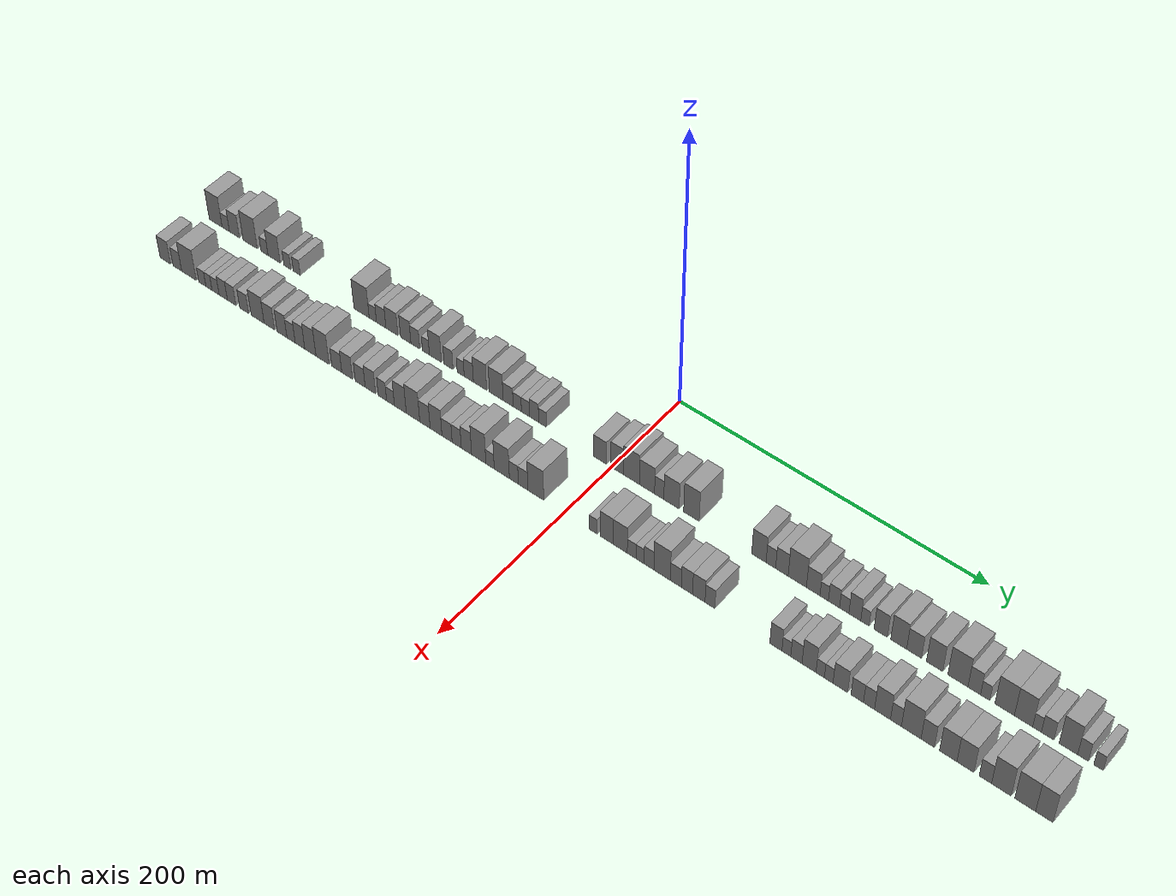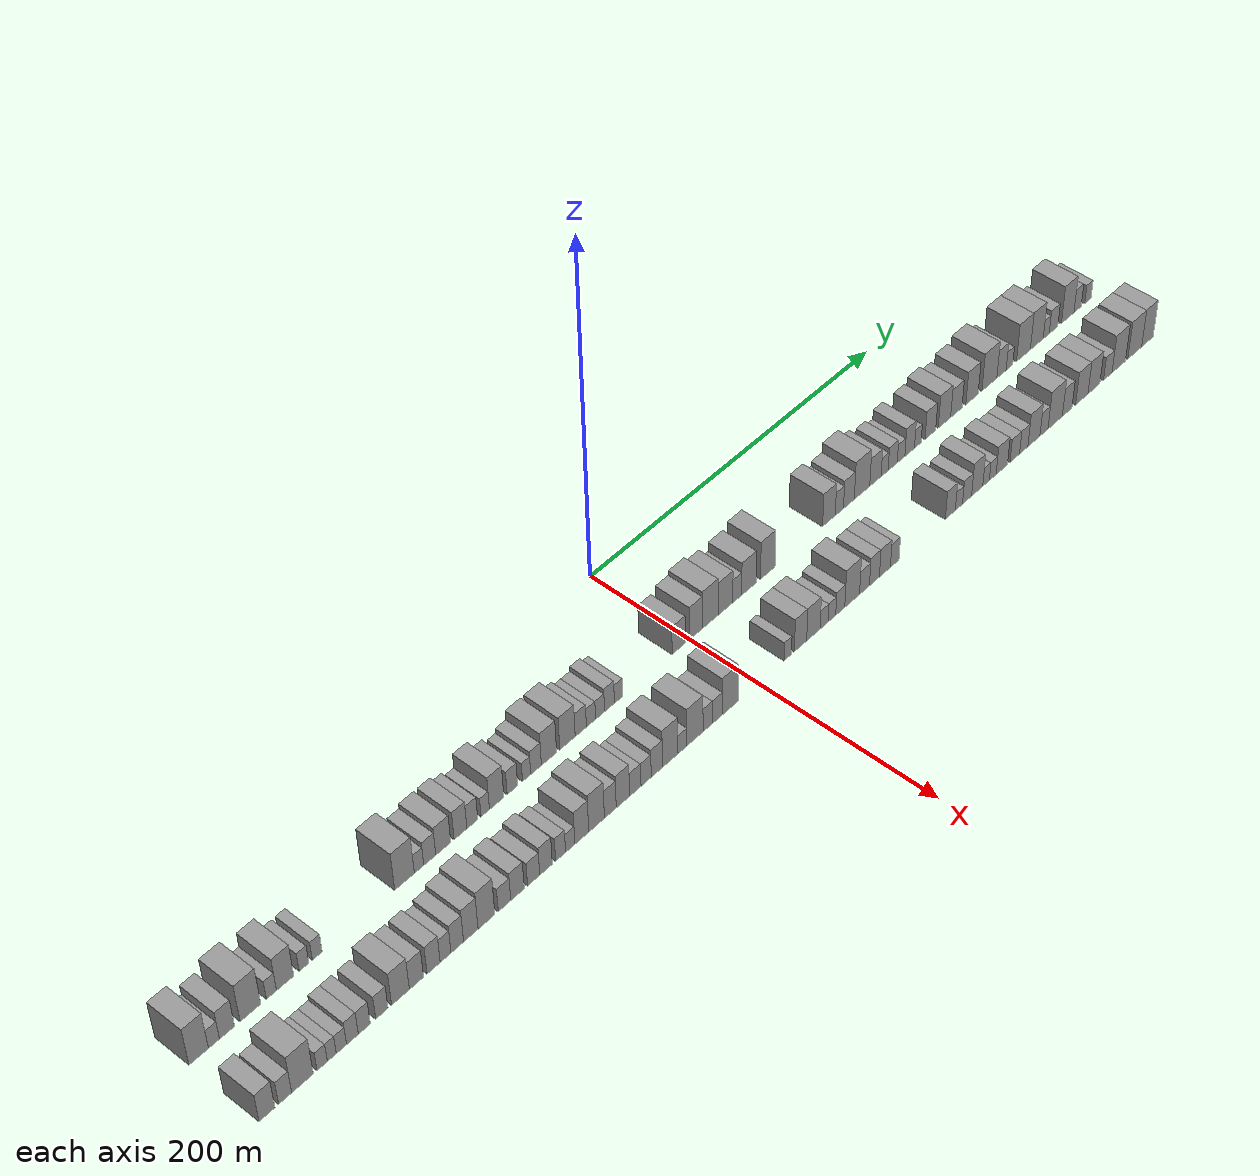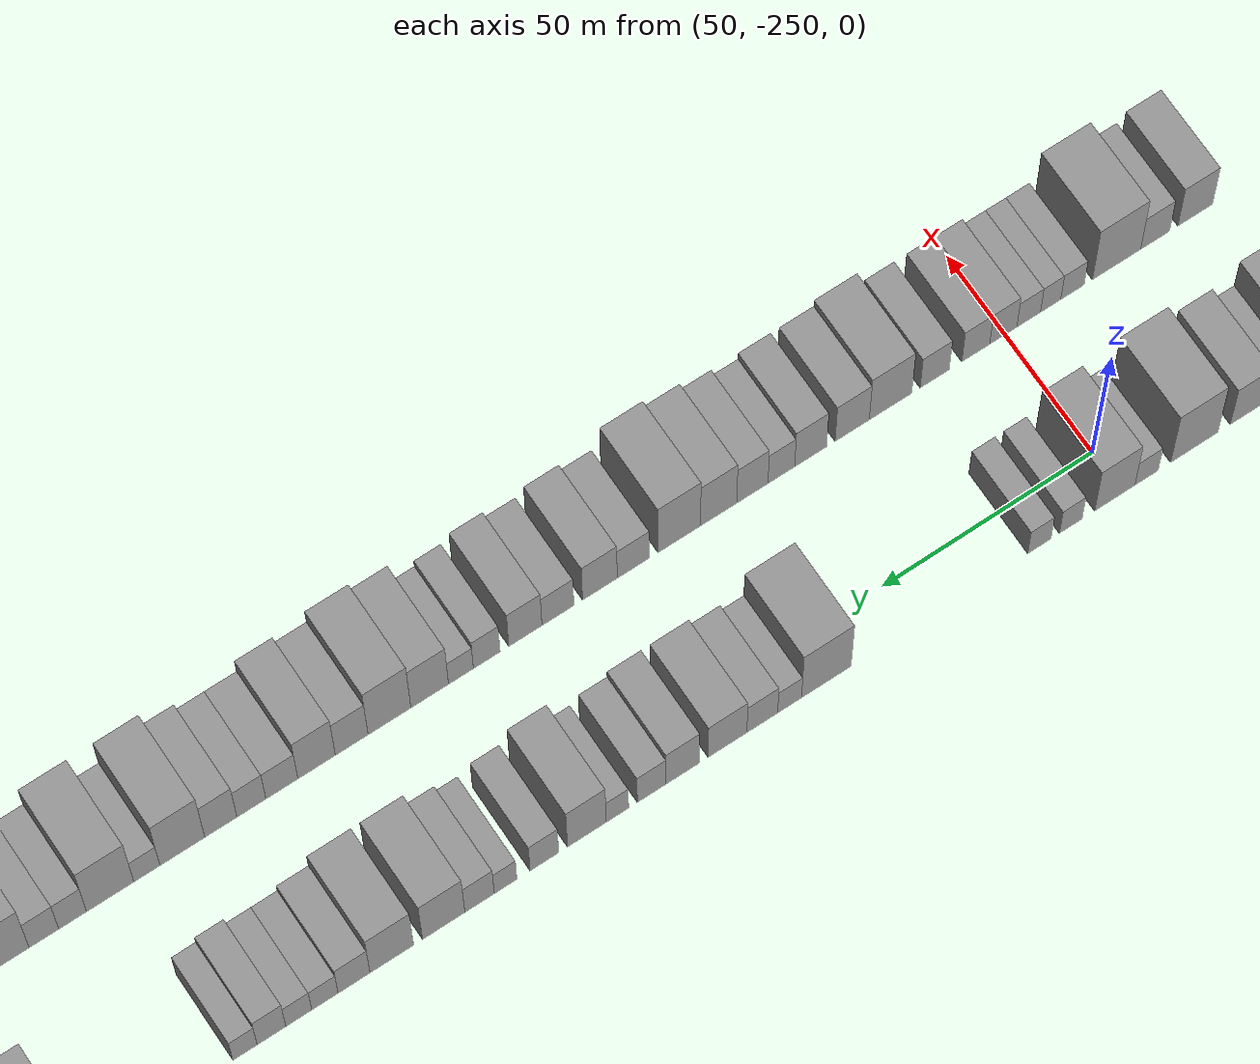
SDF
<sdf version="1.6">
 <world name="default">
  <scene>
   <sky><clouds><speed>12</speed></clouds></sky>
   <ambient>0.4 0.4 0.4 1</ambient>
   <background>0.7 0.7 0.7 1</background>
   <shadows>1</shadows>
  </scene>
  <gravity>0 0 -9.8066</gravity>
  <magnetic_field>6e-06 2.3e-05 -4.2e-05</magnetic_field>
  <physics default="0" name="default_physics" type="ode">
   <ode>
    <solver>
     <type>quick</type>
     <iters>10</iters>
     <sor>1.0</sor>
     <use_dynamic_moi_rescaling>0</use_dynamic_moi_rescaling>
    </solver>
    <constraints>
     <cfm>0</cfm>
     <erp>0.2</erp>
     <contact_max_correcting_vel>100</contact_max_correcting_vel>
     <contact_surface_layer>0.001</contact_surface_layer>
    </constraints>
   </ode>
   <max_step_size>0.004</max_step_size>
   <real_time_factor>1</real_time_factor>
   <real_time_update_rate>250</real_time_update_rate>
  </physics>
  <light name="sun" type="directional">
   <pose>0 0 10 0 0 0</pose>
   <diffuse>0.8 0.8 0.8 1</diffuse>
   <specular>0.2 0.2 0.2 1</specular>
   <attenuation>
    <range>1000</range>
    <constant>0.9</constant>
    <linear>0.01</linear>
    <quadratic>0.001</quadratic>
   </attenuation>
   <direction>-0.5 0.1 -0.9</direction>
  </light>
  <model name="building_1">
   <static>1</static>
   <pose>50.0000 -294.8187 0 0.000000 0.000000 0.000000</pose>
   <link name="link">
    <pose>0 0 12.00 0 0 0</pose>
    <collision name="collision"><geometry><box><size>20.0000 10.3627 24.0000</size></box></geometry></collision>
    <visual name="visual">
     <cast_shadows>0</cast_shadows>
     <geometry><box><size>20.0000 10.3627 24.0000</size></box></geometry>
     <material>
      <script>
       <uri>model://grey_wall/materials/scripts</uri>
       <uri>model://grey_wall/materials/textures</uri>
       <name>vrc/grey_wall</name>
      </script>
     </material>
    </visual>
   </link>
  </model>
  <model name="building_2">
   <static>1</static>
   <pose>50.0000 -286.7062 0 0.000000 0.000000 0.000000</pose>
   <link name="link">
    <pose>0 0 6.00 0 0 0</pose>
    <collision name="collision"><geometry><box><size>20.0000 5.8622 12.0000</size></box></geometry></collision>
    <visual name="visual">
     <cast_shadows>0</cast_shadows>
     <geometry><box><size>20.0000 5.8622 12.0000</size></box></geometry>
     <material>
      <script>
       <uri>model://grey_wall/materials/scripts</uri>
       <uri>model://grey_wall/materials/textures</uri>
       <name>vrc/grey_wall</name>
      </script>
     </material>
    </visual>
   </link>
  </model>
  <model name="building_3">
   <static>1</static>
   <pose>50.0000 -279.7250 0 0.000000 0.000000 0.000000</pose>
   <link name="link">
    <pose>0 0 9.00 0 0 0</pose>
    <collision name="collision"><geometry><box><size>20.0000 8.1002 18.0000</size></box></geometry></collision>
    <visual name="visual">
     <cast_shadows>0</cast_shadows>
     <geometry><box><size>20.0000 8.1002 18.0000</size></box></geometry>
     <material>
      <script>
       <uri>model://grey_wall/materials/scripts</uri>
       <uri>model://grey_wall/materials/textures</uri>
       <name>vrc/grey_wall</name>
      </script>
     </material>
    </visual>
   </link>
  </model>
  <model name="building_4">
   <static>1</static>
   <pose>50.0000 -267.0252 0 0.000000 0.000000 0.000000</pose>
   <link name="link">
    <pose>0 0 12.00 0 0 0</pose>
    <collision name="collision"><geometry><box><size>20.0000 11.2994 24.0000</size></box></geometry></collision>
    <visual name="visual">
     <cast_shadows>0</cast_shadows>
     <geometry><box><size>20.0000 11.2994 24.0000</size></box></geometry>
     <material>
      <script>
       <uri>model://grey_wall/materials/scripts</uri>
       <uri>model://grey_wall/materials/textures</uri>
       <name>vrc/grey_wall</name>
      </script>
     </material>
    </visual>
   </link>
  </model>
  <model name="building_5">
   <static>1</static>
   <pose>50.0000 -255.5983 0 0.000000 0.000000 0.000000</pose>
   <link name="link">
    <pose>0 0 6.00 0 0 0</pose>
    <collision name="collision"><geometry><box><size>20.0000 5.5545 12.0000</size></box></geometry></collision>
    <visual name="visual">
     <cast_shadows>0</cast_shadows>
     <geometry><box><size>20.0000 5.5545 12.0000</size></box></geometry>
     <material>
      <script>
       <uri>model://grey_wall/materials/scripts</uri>
       <uri>model://grey_wall/materials/textures</uri>
       <name>vrc/grey_wall</name>
      </script>
     </material>
    </visual>
   </link>
  </model>
  <model name="building_6">
   <static>1</static>
   <pose>50.0000 -248.0310 0 0.000000 0.000000 0.000000</pose>
   <link name="link">
    <pose>0 0 10.50 0 0 0</pose>
    <collision name="collision"><geometry><box><size>20.0000 9.5799 21.0000</size></box></geometry></collision>
    <visual name="visual">
     <cast_shadows>0</cast_shadows>
     <geometry><box><size>20.0000 9.5799 21.0000</size></box></geometry>
     <material>
      <script>
       <uri>model://grey_wall/materials/scripts</uri>
       <uri>model://grey_wall/materials/textures</uri>
       <name>vrc/grey_wall</name>
      </script>
     </material>
    </visual>
   </link>
  </model>
  <model name="building_7">
   <static>1</static>
   <pose>50.0000 -237.5482 0 0.000000 0.000000 0.000000</pose>
   <link name="link">
    <pose>0 0 6.00 0 0 0</pose>
    <collision name="collision"><geometry><box><size>20.0000 5.3857 12.0000</size></box></geometry></collision>
    <visual name="visual">
     <cast_shadows>0</cast_shadows>
     <geometry><box><size>20.0000 5.3857 12.0000</size></box></geometry>
     <material>
      <script>
       <uri>model://grey_wall/materials/scripts</uri>
       <uri>model://grey_wall/materials/textures</uri>
       <name>vrc/grey_wall</name>
      </script>
     </material>
    </visual>
   </link>
  </model>
  <model name="building_8">
   <static>1</static>
   <pose>50.0000 -230.1114 0 0.000000 0.000000 0.000000</pose>
   <link name="link">
    <pose>0 0 6.00 0 0 0</pose>
    <collision name="collision"><geometry><box><size>20.0000 5.4879 12.0000</size></box></geometry></collision>
    <visual name="visual">
     <cast_shadows>0</cast_shadows>
     <geometry><box><size>20.0000 5.4879 12.0000</size></box></geometry>
     <material>
      <script>
       <uri>model://grey_wall/materials/scripts</uri>
       <uri>model://grey_wall/materials/textures</uri>
       <name>vrc/grey_wall</name>
      </script>
     </material>
    </visual>
   </link>
  </model>
  <model name="building_9">
   <static>1</static>
   <pose>50.0000 -180.0777 0 0.000000 0.000000 0.000000</pose>
   <link name="link">
    <pose>0 0 12.00 0 0 0</pose>
    <collision name="collision"><geometry><box><size>20.0000 11.5265 24.0000</size></box></geometry></collision>
    <visual name="visual">
     <cast_shadows>0</cast_shadows>
     <geometry><box><size>20.0000 11.5265 24.0000</size></box></geometry>
     <material>
      <script>
       <uri>model://grey_wall/materials/scripts</uri>
       <uri>model://grey_wall/materials/textures</uri>
       <name>vrc/grey_wall</name>
      </script>
     </material>
    </visual>
   </link>
  </model>
  <model name="building_10">
   <static>1</static>
   <pose>50.0000 -171.5470 0 0.000000 0.000000 0.000000</pose>
   <link name="link">
    <pose>0 0 6.00 0 0 0</pose>
    <collision name="collision"><geometry><box><size>20.0000 5.5348 12.0000</size></box></geometry></collision>
    <visual name="visual">
     <cast_shadows>0</cast_shadows>
     <geometry><box><size>20.0000 5.5348 12.0000</size></box></geometry>
     <material>
      <script>
       <uri>model://grey_wall/materials/scripts</uri>
       <uri>model://grey_wall/materials/textures</uri>
       <name>vrc/grey_wall</name>
      </script>
     </material>
    </visual>
   </link>
  </model>
  <model name="building_11">
   <static>1</static>
   <pose>50.0000 -165.2122 0 0.000000 0.000000 0.000000</pose>
   <link name="link">
    <pose>0 0 7.50 0 0 0</pose>
    <collision name="collision"><geometry><box><size>20.0000 7.1348 15.0000</size></box></geometry></collision>
    <visual name="visual">
     <cast_shadows>0</cast_shadows>
     <geometry><box><size>20.0000 7.1348 15.0000</size></box></geometry>
     <material>
      <script>
       <uri>model://grey_wall/materials/scripts</uri>
       <uri>model://grey_wall/materials/textures</uri>
       <name>vrc/grey_wall</name>
      </script>
     </material>
    </visual>
   </link>
  </model>
  <model name="building_12">
   <static>1</static>
   <pose>50.0000 -157.1682 0 0.000000 0.000000 0.000000</pose>
   <link name="link">
    <pose>0 0 9.00 0 0 0</pose>
    <collision name="collision"><geometry><box><size>20.0000 8.9532 18.0000</size></box></geometry></collision>
    <visual name="visual">
     <cast_shadows>0</cast_shadows>
     <geometry><box><size>20.0000 8.9532 18.0000</size></box></geometry>
     <material>
      <script>
       <uri>model://grey_wall/materials/scripts</uri>
       <uri>model://grey_wall/materials/textures</uri>
       <name>vrc/grey_wall</name>
      </script>
     </material>
    </visual>
   </link>
  </model>
  <model name="building_13">
   <static>1</static>
   <pose>50.0000 -146.8314 0 0.000000 0.000000 0.000000</pose>
   <link name="link">
    <pose>0 0 9.00 0 0 0</pose>
    <collision name="collision"><geometry><box><size>20.0000 7.7205 18.0000</size></box></geometry></collision>
    <visual name="visual">
     <cast_shadows>0</cast_shadows>
     <geometry><box><size>20.0000 7.7205 18.0000</size></box></geometry>
     <material>
      <script>
       <uri>model://grey_wall/materials/scripts</uri>
       <uri>model://grey_wall/materials/textures</uri>
       <name>vrc/grey_wall</name>
      </script>
     </material>
    </visual>
   </link>
  </model>
  <model name="building_14">
   <static>1</static>
   <pose>50.0000 -139.6915 0 0.000000 0.000000 0.000000</pose>
   <link name="link">
    <pose>0 0 7.50 0 0 0</pose>
    <collision name="collision"><geometry><box><size>20.0000 6.5593 15.0000</size></box></geometry></collision>
    <visual name="visual">
     <cast_shadows>0</cast_shadows>
     <geometry><box><size>20.0000 6.5593 15.0000</size></box></geometry>
     <material>
      <script>
       <uri>model://grey_wall/materials/scripts</uri>
       <uri>model://grey_wall/materials/textures</uri>
       <name>vrc/grey_wall</name>
      </script>
     </material>
    </visual>
   </link>
  </model>
  <model name="building_15">
   <static>1</static>
   <pose>50.0000 -131.8465 0 0.000000 0.000000 0.000000</pose>
   <link name="link">
    <pose>0 0 6.00 0 0 0</pose>
    <collision name="collision"><geometry><box><size>20.0000 5.1307 12.0000</size></box></geometry></collision>
    <visual name="visual">
     <cast_shadows>0</cast_shadows>
     <geometry><box><size>20.0000 5.1307 12.0000</size></box></geometry>
     <material>
      <script>
       <uri>model://grey_wall/materials/scripts</uri>
       <uri>model://grey_wall/materials/textures</uri>
       <name>vrc/grey_wall</name>
      </script>
     </material>
    </visual>
   </link>
  </model>
  <model name="building_16">
   <static>1</static>
   <pose>50.0000 -124.8556 0 0.000000 0.000000 0.000000</pose>
   <link name="link">
    <pose>0 0 10.50 0 0 0</pose>
    <collision name="collision"><geometry><box><size>20.0000 8.8511 21.0000</size></box></geometry></collision>
    <visual name="visual">
     <cast_shadows>0</cast_shadows>
     <geometry><box><size>20.0000 8.8511 21.0000</size></box></geometry>
     <material>
      <script>
       <uri>model://grey_wall/materials/scripts</uri>
       <uri>model://grey_wall/materials/textures</uri>
       <name>vrc/grey_wall</name>
      </script>
     </material>
    </visual>
   </link>
  </model>
  <model name="building_17">
   <static>1</static>
   <pose>50.0000 -115.1703 0 0.000000 0.000000 0.000000</pose>
   <link name="link">
    <pose>0 0 7.50 0 0 0</pose>
    <collision name="collision"><geometry><box><size>20.0000 6.5195 15.0000</size></box></geometry></collision>
    <visual name="visual">
     <cast_shadows>0</cast_shadows>
     <geometry><box><size>20.0000 6.5195 15.0000</size></box></geometry>
     <material>
      <script>
       <uri>model://grey_wall/materials/scripts</uri>
       <uri>model://grey_wall/materials/textures</uri>
       <name>vrc/grey_wall</name>
      </script>
     </material>
    </visual>
   </link>
  </model>
  <model name="building_18">
   <static>1</static>
   <pose>50.0000 -106.3521 0 0.000000 0.000000 0.000000</pose>
   <link name="link">
    <pose>0 0 6.00 0 0 0</pose>
    <collision name="collision"><geometry><box><size>20.0000 5.1170 12.0000</size></box></geometry></collision>
    <visual name="visual">
     <cast_shadows>0</cast_shadows>
     <geometry><box><size>20.0000 5.1170 12.0000</size></box></geometry>
     <material>
      <script>
       <uri>model://grey_wall/materials/scripts</uri>
       <uri>model://grey_wall/materials/textures</uri>
       <name>vrc/grey_wall</name>
      </script>
     </material>
    </visual>
   </link>
  </model>
  <model name="building_19">
   <static>1</static>
   <pose>50.0000 -100.4487 0 0.000000 0.000000 0.000000</pose>
   <link name="link">
    <pose>0 0 7.50 0 0 0</pose>
    <collision name="collision"><geometry><box><size>20.0000 6.6897 15.0000</size></box></geometry></collision>
    <visual name="visual">
     <cast_shadows>0</cast_shadows>
     <geometry><box><size>20.0000 6.6897 15.0000</size></box></geometry>
     <material>
      <script>
       <uri>model://grey_wall/materials/scripts</uri>
       <uri>model://grey_wall/materials/textures</uri>
       <name>vrc/grey_wall</name>
      </script>
     </material>
    </visual>
   </link>
  </model>
  <model name="building_20">
   <static>1</static>
   <pose>50.0000 -92.3190 0 0.000000 0.000000 0.000000</pose>
   <link name="link">
    <pose>0 0 10.50 0 0 0</pose>
    <collision name="collision"><geometry><box><size>20.0000 9.5698 21.0000</size></box></geometry></collision>
    <visual name="visual">
     <cast_shadows>0</cast_shadows>
     <geometry><box><size>20.0000 9.5698 21.0000</size></box></geometry>
     <material>
      <script>
       <uri>model://grey_wall/materials/scripts</uri>
       <uri>model://grey_wall/materials/textures</uri>
       <name>vrc/grey_wall</name>
      </script>
     </material>
    </visual>
   </link>
  </model>
  <model name="building_21">
   <static>1</static>
   <pose>50.0000 -80.6359 0 0.000000 0.000000 0.000000</pose>
   <link name="link">
    <pose>0 0 10.50 0 0 0</pose>
    <collision name="collision"><geometry><box><size>20.0000 9.7964 21.0000</size></box></geometry></collision>
    <visual name="visual">
     <cast_shadows>0</cast_shadows>
     <geometry><box><size>20.0000 9.7964 21.0000</size></box></geometry>
     <material>
      <script>
       <uri>model://grey_wall/materials/scripts</uri>
       <uri>model://grey_wall/materials/textures</uri>
       <name>vrc/grey_wall</name>
      </script>
     </material>
    </visual>
   </link>
  </model>
  <model name="building_22">
   <static>1</static>
   <pose>50.0000 -72.1522 0 0.000000 0.000000 0.000000</pose>
   <link name="link">
    <pose>0 0 7.50 0 0 0</pose>
    <collision name="collision"><geometry><box><size>20.0000 7.1708 15.0000</size></box></geometry></collision>
    <visual name="visual">
     <cast_shadows>0</cast_shadows>
     <geometry><box><size>20.0000 7.1708 15.0000</size></box></geometry>
     <material>
      <script>
       <uri>model://grey_wall/materials/scripts</uri>
       <uri>model://grey_wall/materials/textures</uri>
       <name>vrc/grey_wall</name>
      </script>
     </material>
    </visual>
   </link>
  </model>
  <model name="building_23">
   <static>1</static>
   <pose>50.0000 -65.6227 0 0.000000 0.000000 0.000000</pose>
   <link name="link">
    <pose>0 0 6.00 0 0 0</pose>
    <collision name="collision"><geometry><box><size>20.0000 5.8883 12.0000</size></box></geometry></collision>
    <visual name="visual">
     <cast_shadows>0</cast_shadows>
     <geometry><box><size>20.0000 5.8883 12.0000</size></box></geometry>
     <material>
      <script>
       <uri>model://grey_wall/materials/scripts</uri>
       <uri>model://grey_wall/materials/textures</uri>
       <name>vrc/grey_wall</name>
      </script>
     </material>
    </visual>
   </link>
  </model>
  <model name="building_24">
   <static>1</static>
   <pose>50.0000 -59.7776 0 0.000000 0.000000 0.000000</pose>
   <link name="link">
    <pose>0 0 6.00 0 0 0</pose>
    <collision name="collision"><geometry><box><size>20.0000 5.8018 12.0000</size></box></geometry></collision>
    <visual name="visual">
     <cast_shadows>0</cast_shadows>
     <geometry><box><size>20.0000 5.8018 12.0000</size></box></geometry>
     <material>
      <script>
       <uri>model://grey_wall/materials/scripts</uri>
       <uri>model://grey_wall/materials/textures</uri>
       <name>vrc/grey_wall</name>
      </script>
     </material>
    </visual>
   </link>
  </model>
  <model name="building_25">
   <static>1</static>
   <pose>50.0000 -53.6754 0 0.000000 0.000000 0.000000</pose>
   <link name="link">
    <pose>0 0 7.50 0 0 0</pose>
    <collision name="collision"><geometry><box><size>20.0000 6.4025 15.0000</size></box></geometry></collision>
    <visual name="visual">
     <cast_shadows>0</cast_shadows>
     <geometry><box><size>20.0000 6.4025 15.0000</size></box></geometry>
     <material>
      <script>
       <uri>model://grey_wall/materials/scripts</uri>
       <uri>model://grey_wall/materials/textures</uri>
       <name>vrc/grey_wall</name>
      </script>
     </material>
    </visual>
   </link>
  </model>
  <model name="building_26">
   <static>1</static>
   <pose>50.0000 -47.7760 0 0.000000 0.000000 0.000000</pose>
   <link name="link">
    <pose>0 0 6.00 0 0 0</pose>
    <collision name="collision"><geometry><box><size>20.0000 5.3963 12.0000</size></box></geometry></collision>
    <visual name="visual">
     <cast_shadows>0</cast_shadows>
     <geometry><box><size>20.0000 5.3963 12.0000</size></box></geometry>
     <material>
      <script>
       <uri>model://grey_wall/materials/scripts</uri>
       <uri>model://grey_wall/materials/textures</uri>
       <name>vrc/grey_wall</name>
      </script>
     </material>
    </visual>
   </link>
  </model>
  <model name="building_27">
   <static>1</static>
   <pose>50.0000 -7.8816 0 0.000000 0.000000 0.000000</pose>
   <link name="link">
    <pose>0 0 9.00 0 0 0</pose>
    <collision name="collision"><geometry><box><size>20.0000 8.7975 18.0000</size></box></geometry></collision>
    <visual name="visual">
     <cast_shadows>0</cast_shadows>
     <geometry><box><size>20.0000 8.7975 18.0000</size></box></geometry>
     <material>
      <script>
       <uri>model://grey_wall/materials/scripts</uri>
       <uri>model://grey_wall/materials/textures</uri>
       <name>vrc/grey_wall</name>
      </script>
     </material>
    </visual>
   </link>
  </model>
  <model name="building_28">
   <static>1</static>
   <pose>50.0000 3.8579 0 0.000000 0.000000 0.000000</pose>
   <link name="link">
    <pose>0 0 10.50 0 0 0</pose>
    <collision name="collision"><geometry><box><size>20.0000 8.6814 21.0000</size></box></geometry></collision>
    <visual name="visual">
     <cast_shadows>0</cast_shadows>
     <geometry><box><size>20.0000 8.6814 21.0000</size></box></geometry>
     <material>
      <script>
       <uri>model://grey_wall/materials/scripts</uri>
       <uri>model://grey_wall/materials/textures</uri>
       <name>vrc/grey_wall</name>
      </script>
     </material>
    </visual>
   </link>
  </model>
  <model name="building_29">
   <static>1</static>
   <pose>50.0000 13.5751 0 0.000000 0.000000 0.000000</pose>
   <link name="link">
    <pose>0 0 12.00 0 0 0</pose>
    <collision name="collision"><geometry><box><size>20.0000 10.7529 24.0000</size></box></geometry></collision>
    <visual name="visual">
     <cast_shadows>0</cast_shadows>
     <geometry><box><size>20.0000 10.7529 24.0000</size></box></geometry>
     <material>
      <script>
       <uri>model://grey_wall/materials/scripts</uri>
       <uri>model://grey_wall/materials/textures</uri>
       <name>vrc/grey_wall</name>
      </script>
     </material>
    </visual>
   </link>
  </model>
  <model name="building_30">
   <static>1</static>
   <pose>50.0000 24.0050 0 0.000000 0.000000 0.000000</pose>
   <link name="link">
    <pose>0 0 10.50 0 0 0</pose>
    <collision name="collision"><geometry><box><size>20.0000 10.1068 21.0000</size></box></geometry></collision>
    <visual name="visual">
     <cast_shadows>0</cast_shadows>
     <geometry><box><size>20.0000 10.1068 21.0000</size></box></geometry>
     <material>
      <script>
       <uri>model://grey_wall/materials/scripts</uri>
       <uri>model://grey_wall/materials/textures</uri>
       <name>vrc/grey_wall</name>
      </script>
     </material>
    </visual>
   </link>
  </model>
  <model name="building_31">
   <static>1</static>
   <pose>50.0000 32.1459 0 0.000000 0.000000 0.000000</pose>
   <link name="link">
    <pose>0 0 7.50 0 0 0</pose>
    <collision name="collision"><geometry><box><size>20.0000 6.1750 15.0000</size></box></geometry></collision>
    <visual name="visual">
     <cast_shadows>0</cast_shadows>
     <geometry><box><size>20.0000 6.1750 15.0000</size></box></geometry>
     <material>
      <script>
       <uri>model://grey_wall/materials/scripts</uri>
       <uri>model://grey_wall/materials/textures</uri>
       <name>vrc/grey_wall</name>
      </script>
     </material>
    </visual>
   </link>
  </model>
  <model name="building_32">
   <static>1</static>
   <pose>50.0000 40.3316 0 0.000000 0.000000 0.000000</pose>
   <link name="link">
    <pose>0 0 10.50 0 0 0</pose>
    <collision name="collision"><geometry><box><size>20.0000 10.1965 21.0000</size></box></geometry></collision>
    <visual name="visual">
     <cast_shadows>0</cast_shadows>
     <geometry><box><size>20.0000 10.1965 21.0000</size></box></geometry>
     <material>
      <script>
       <uri>model://grey_wall/materials/scripts</uri>
       <uri>model://grey_wall/materials/textures</uri>
       <name>vrc/grey_wall</name>
      </script>
     </material>
    </visual>
   </link>
  </model>
  <model name="building_33">
   <static>1</static>
   <pose>50.0000 53.5483 0 0.000000 0.000000 0.000000</pose>
   <link name="link">
    <pose>0 0 12.00 0 0 0</pose>
    <collision name="collision"><geometry><box><size>20.0000 10.2368 24.0000</size></box></geometry></collision>
    <visual name="visual">
     <cast_shadows>0</cast_shadows>
     <geometry><box><size>20.0000 10.2368 24.0000</size></box></geometry>
     <material>
      <script>
       <uri>model://grey_wall/materials/scripts</uri>
       <uri>model://grey_wall/materials/textures</uri>
       <name>vrc/grey_wall</name>
      </script>
     </material>
    </visual>
   </link>
  </model>
  <model name="building_34">
   <static>1</static>
   <pose>50.0000 97.4799 0 0.000000 0.000000 0.000000</pose>
   <link name="link">
    <pose>0 0 10.50 0 0 0</pose>
    <collision name="collision"><geometry><box><size>20.0000 9.2088 21.0000</size></box></geometry></collision>
    <visual name="visual">
     <cast_shadows>0</cast_shadows>
     <geometry><box><size>20.0000 9.2088 21.0000</size></box></geometry>
     <material>
      <script>
       <uri>model://grey_wall/materials/scripts</uri>
       <uri>model://grey_wall/materials/textures</uri>
       <name>vrc/grey_wall</name>
      </script>
     </material>
    </visual>
   </link>
  </model>
  <model name="building_35">
   <static>1</static>
   <pose>50.0000 105.1145 0 0.000000 0.000000 0.000000</pose>
   <link name="link">
    <pose>0 0 7.50 0 0 0</pose>
    <collision name="collision"><geometry><box><size>20.0000 6.0606 15.0000</size></box></geometry></collision>
    <visual name="visual">
     <cast_shadows>0</cast_shadows>
     <geometry><box><size>20.0000 6.0606 15.0000</size></box></geometry>
     <material>
      <script>
       <uri>model://grey_wall/materials/scripts</uri>
       <uri>model://grey_wall/materials/textures</uri>
       <name>vrc/grey_wall</name>
      </script>
     </material>
    </visual>
   </link>
  </model>
  <model name="building_36">
   <static>1</static>
   <pose>50.0000 112.1290 0 0.000000 0.000000 0.000000</pose>
   <link name="link">
    <pose>0 0 9.00 0 0 0</pose>
    <collision name="collision"><geometry><box><size>20.0000 7.9685 18.0000</size></box></geometry></collision>
    <visual name="visual">
     <cast_shadows>0</cast_shadows>
     <geometry><box><size>20.0000 7.9685 18.0000</size></box></geometry>
     <material>
      <script>
       <uri>model://grey_wall/materials/scripts</uri>
       <uri>model://grey_wall/materials/textures</uri>
       <name>vrc/grey_wall</name>
      </script>
     </material>
    </visual>
   </link>
  </model>
  <model name="building_37">
   <static>1</static>
   <pose>50.0000 121.8683 0 0.000000 0.000000 0.000000</pose>
   <link name="link">
    <pose>0 0 12.00 0 0 0</pose>
    <collision name="collision"><geometry><box><size>20.0000 11.5101 24.0000</size></box></geometry></collision>
    <visual name="visual">
     <cast_shadows>0</cast_shadows>
     <geometry><box><size>20.0000 11.5101 24.0000</size></box></geometry>
     <material>
      <script>
       <uri>model://grey_wall/materials/scripts</uri>
       <uri>model://grey_wall/materials/textures</uri>
       <name>vrc/grey_wall</name>
      </script>
     </material>
    </visual>
   </link>
  </model>
  <model name="building_38">
   <static>1</static>
   <pose>50.0000 131.8711 0 0.000000 0.000000 0.000000</pose>
   <link name="link">
    <pose>0 0 9.00 0 0 0</pose>
    <collision name="collision"><geometry><box><size>20.0000 8.4955 18.0000</size></box></geometry></collision>
    <visual name="visual">
     <cast_shadows>0</cast_shadows>
     <geometry><box><size>20.0000 8.4955 18.0000</size></box></geometry>
     <material>
      <script>
       <uri>model://grey_wall/materials/scripts</uri>
       <uri>model://grey_wall/materials/textures</uri>
       <name>vrc/grey_wall</name>
      </script>
     </material>
    </visual>
   </link>
  </model>
  <model name="building_39">
   <static>1</static>
   <pose>50.0000 138.7568 0 0.000000 0.000000 0.000000</pose>
   <link name="link">
    <pose>0 0 6.00 0 0 0</pose>
    <collision name="collision"><geometry><box><size>20.0000 5.2759 12.0000</size></box></geometry></collision>
    <visual name="visual">
     <cast_shadows>0</cast_shadows>
     <geometry><box><size>20.0000 5.2759 12.0000</size></box></geometry>
     <material>
      <script>
       <uri>model://grey_wall/materials/scripts</uri>
       <uri>model://grey_wall/materials/textures</uri>
       <name>vrc/grey_wall</name>
      </script>
     </material>
    </visual>
   </link>
  </model>
  <model name="building_40">
   <static>1</static>
   <pose>50.0000 144.8671 0 0.000000 0.000000 0.000000</pose>
   <link name="link">
    <pose>0 0 7.50 0 0 0</pose>
    <collision name="collision"><geometry><box><size>20.0000 6.9448 15.0000</size></box></geometry></collision>
    <visual name="visual">
     <cast_shadows>0</cast_shadows>
     <geometry><box><size>20.0000 6.9448 15.0000</size></box></geometry>
     <material>
      <script>
       <uri>model://grey_wall/materials/scripts</uri>
       <uri>model://grey_wall/materials/textures</uri>
       <name>vrc/grey_wall</name>
      </script>
     </material>
    </visual>
   </link>
  </model>
  <model name="building_41">
   <static>1</static>
   <pose>50.0000 151.2323 0 0.000000 0.000000 0.000000</pose>
   <link name="link">
    <pose>0 0 6.00 0 0 0</pose>
    <collision name="collision"><geometry><box><size>20.0000 5.7856 12.0000</size></box></geometry></collision>
    <visual name="visual">
     <cast_shadows>0</cast_shadows>
     <geometry><box><size>20.0000 5.7856 12.0000</size></box></geometry>
     <material>
      <script>
       <uri>model://grey_wall/materials/scripts</uri>
       <uri>model://grey_wall/materials/textures</uri>
       <name>vrc/grey_wall</name>
      </script>
     </material>
    </visual>
   </link>
  </model>
  <model name="building_42">
   <static>1</static>
   <pose>50.0000 157.7852 0 0.000000 0.000000 0.000000</pose>
   <link name="link">
    <pose>0 0 9.00 0 0 0</pose>
    <collision name="collision"><geometry><box><size>20.0000 7.3201 18.0000</size></box></geometry></collision>
    <visual name="visual">
     <cast_shadows>0</cast_shadows>
     <geometry><box><size>20.0000 7.3201 18.0000</size></box></geometry>
     <material>
      <script>
       <uri>model://grey_wall/materials/scripts</uri>
       <uri>model://grey_wall/materials/textures</uri>
       <name>vrc/grey_wall</name>
      </script>
     </material>
    </visual>
   </link>
  </model>
  <model name="building_43">
   <static>1</static>
   <pose>50.0000 164.0114 0 0.000000 0.000000 0.000000</pose>
   <link name="link">
    <pose>0 0 6.00 0 0 0</pose>
    <collision name="collision"><geometry><box><size>20.0000 5.1324 12.0000</size></box></geometry></collision>
    <visual name="visual">
     <cast_shadows>0</cast_shadows>
     <geometry><box><size>20.0000 5.1324 12.0000</size></box></geometry>
     <material>
      <script>
       <uri>model://grey_wall/materials/scripts</uri>
       <uri>model://grey_wall/materials/textures</uri>
       <name>vrc/grey_wall</name>
      </script>
     </material>
    </visual>
   </link>
  </model>
  <model name="building_44">
   <static>1</static>
   <pose>50.0000 173.6840 0 0.000000 0.000000 0.000000</pose>
   <link name="link">
    <pose>0 0 9.00 0 0 0</pose>
    <collision name="collision"><geometry><box><size>20.0000 8.2128 18.0000</size></box></geometry></collision>
    <visual name="visual">
     <cast_shadows>0</cast_shadows>
     <geometry><box><size>20.0000 8.2128 18.0000</size></box></geometry>
     <material>
      <script>
       <uri>model://grey_wall/materials/scripts</uri>
       <uri>model://grey_wall/materials/textures</uri>
       <name>vrc/grey_wall</name>
      </script>
     </material>
    </visual>
   </link>
  </model>
  <model name="building_45">
   <static>1</static>
   <pose>50.0000 184.6107 0 0.000000 0.000000 0.000000</pose>
   <link name="link">
    <pose>0 0 10.50 0 0 0</pose>
    <collision name="collision"><geometry><box><size>20.0000 9.6407 21.0000</size></box></geometry></collision>
    <visual name="visual">
     <cast_shadows>0</cast_shadows>
     <geometry><box><size>20.0000 9.6407 21.0000</size></box></geometry>
     <material>
      <script>
       <uri>model://grey_wall/materials/scripts</uri>
       <uri>model://grey_wall/materials/textures</uri>
       <name>vrc/grey_wall</name>
      </script>
     </material>
    </visual>
   </link>
  </model>
  <model name="building_46">
   <static>1</static>
   <pose>50.0000 193.9039 0 0.000000 0.000000 0.000000</pose>
   <link name="link">
    <pose>0 0 9.00 0 0 0</pose>
    <collision name="collision"><geometry><box><size>20.0000 8.9455 18.0000</size></box></geometry></collision>
    <visual name="visual">
     <cast_shadows>0</cast_shadows>
     <geometry><box><size>20.0000 8.9455 18.0000</size></box></geometry>
     <material>
      <script>
       <uri>model://grey_wall/materials/scripts</uri>
       <uri>model://grey_wall/materials/textures</uri>
       <name>vrc/grey_wall</name>
      </script>
     </material>
    </visual>
   </link>
  </model>
  <model name="building_47">
   <static>1</static>
   <pose>50.0000 206.2515 0 0.000000 0.000000 0.000000</pose>
   <link name="link">
    <pose>0 0 10.50 0 0 0</pose>
    <collision name="collision"><geometry><box><size>20.0000 9.7498 21.0000</size></box></geometry></collision>
    <visual name="visual">
     <cast_shadows>0</cast_shadows>
     <geometry><box><size>20.0000 9.7498 21.0000</size></box></geometry>
     <material>
      <script>
       <uri>model://grey_wall/materials/scripts</uri>
       <uri>model://grey_wall/materials/textures</uri>
       <name>vrc/grey_wall</name>
      </script>
     </material>
    </visual>
   </link>
  </model>
  <model name="building_48">
   <static>1</static>
   <pose>50.0000 220.0855 0 0.000000 0.000000 0.000000</pose>
   <link name="link">
    <pose>0 0 12.00 0 0 0</pose>
    <collision name="collision"><geometry><box><size>20.0000 11.9182 24.0000</size></box></geometry></collision>
    <visual name="visual">
     <cast_shadows>0</cast_shadows>
     <geometry><box><size>20.0000 11.9182 24.0000</size></box></geometry>
     <material>
      <script>
       <uri>model://grey_wall/materials/scripts</uri>
       <uri>model://grey_wall/materials/textures</uri>
       <name>vrc/grey_wall</name>
      </script>
     </material>
    </visual>
   </link>
  </model>
  <model name="building_49">
   <static>1</static>
   <pose>50.0000 229.7519 0 0.000000 0.000000 0.000000</pose>
   <link name="link">
    <pose>0 0 9.00 0 0 0</pose>
    <collision name="collision"><geometry><box><size>20.0000 7.4147 18.0000</size></box></geometry></collision>
    <visual name="visual">
     <cast_shadows>0</cast_shadows>
     <geometry><box><size>20.0000 7.4147 18.0000</size></box></geometry>
     <material>
      <script>
       <uri>model://grey_wall/materials/scripts</uri>
       <uri>model://grey_wall/materials/textures</uri>
       <name>vrc/grey_wall</name>
      </script>
     </material>
    </visual>
   </link>
  </model>
  <model name="building_50">
   <static>1</static>
   <pose>50.0000 236.1665 0 0.000000 0.000000 0.000000</pose>
   <link name="link">
    <pose>0 0 6.00 0 0 0</pose>
    <collision name="collision"><geometry><box><size>20.0000 5.4144 12.0000</size></box></geometry></collision>
    <visual name="visual">
     <cast_shadows>0</cast_shadows>
     <geometry><box><size>20.0000 5.4144 12.0000</size></box></geometry>
     <material>
      <script>
       <uri>model://grey_wall/materials/scripts</uri>
       <uri>model://grey_wall/materials/textures</uri>
       <name>vrc/grey_wall</name>
      </script>
     </material>
    </visual>
   </link>
  </model>
  <model name="building_51">
   <static>1</static>
   <pose>50.0000 247.5233 0 0.000000 0.000000 0.000000</pose>
   <link name="link">
    <pose>0 0 12.00 0 0 0</pose>
    <collision name="collision"><geometry><box><size>20.0000 11.2993 24.0000</size></box></geometry></collision>
    <visual name="visual">
     <cast_shadows>0</cast_shadows>
     <geometry><box><size>20.0000 11.2993 24.0000</size></box></geometry>
     <material>
      <script>
       <uri>model://grey_wall/materials/scripts</uri>
       <uri>model://grey_wall/materials/textures</uri>
       <name>vrc/grey_wall</name>
      </script>
     </material>
    </visual>
   </link>
  </model>
  <model name="building_52">
   <static>1</static>
   <pose>50.0000 258.4400 0 0.000000 0.000000 0.000000</pose>
   <link name="link">
    <pose>0 0 12.00 0 0 0</pose>
    <collision name="collision"><geometry><box><size>20.0000 10.5341 24.0000</size></box></geometry></collision>
    <visual name="visual">
     <cast_shadows>0</cast_shadows>
     <geometry><box><size>20.0000 10.5341 24.0000</size></box></geometry>
     <material>
      <script>
       <uri>model://grey_wall/materials/scripts</uri>
       <uri>model://grey_wall/materials/textures</uri>
       <name>vrc/grey_wall</name>
      </script>
     </material>
    </visual>
   </link>
  </model>
  <model name="building_53">
   <static>1</static>
   <pose>50.0000 266.1904 0 0.000000 0.000000 0.000000</pose>
   <link name="link">
    <pose>0 0 6.00 0 0 0</pose>
    <collision name="collision"><geometry><box><size>20.0000 4.9665 12.0000</size></box></geometry></collision>
    <visual name="visual">
     <cast_shadows>0</cast_shadows>
     <geometry><box><size>20.0000 4.9665 12.0000</size></box></geometry>
     <material>
      <script>
       <uri>model://grey_wall/materials/scripts</uri>
       <uri>model://grey_wall/materials/textures</uri>
       <name>vrc/grey_wall</name>
      </script>
     </material>
    </visual>
   </link>
  </model>
  <model name="building_54">
   <static>1</static>
   <pose>50.0000 272.2597 0 0.000000 0.000000 0.000000</pose>
   <link name="link">
    <pose>0 0 7.50 0 0 0</pose>
    <collision name="collision"><geometry><box><size>20.0000 7.1720 15.0000</size></box></geometry></collision>
    <visual name="visual">
     <cast_shadows>0</cast_shadows>
     <geometry><box><size>20.0000 7.1720 15.0000</size></box></geometry>
     <material>
      <script>
       <uri>model://grey_wall/materials/scripts</uri>
       <uri>model://grey_wall/materials/textures</uri>
       <name>vrc/grey_wall</name>
      </script>
     </material>
    </visual>
   </link>
  </model>
  <model name="building_55">
   <static>1</static>
   <pose>50.0000 284.0848 0 0.000000 0.000000 0.000000</pose>
   <link name="link">
    <pose>0 0 12.00 0 0 0</pose>
    <collision name="collision"><geometry><box><size>20.0000 10.4783 24.0000</size></box></geometry></collision>
    <visual name="visual">
     <cast_shadows>0</cast_shadows>
     <geometry><box><size>20.0000 10.4783 24.0000</size></box></geometry>
     <material>
      <script>
       <uri>model://grey_wall/materials/scripts</uri>
       <uri>model://grey_wall/materials/textures</uri>
       <name>vrc/grey_wall</name>
      </script>
     </material>
    </visual>
   </link>
  </model>
  <model name="building_56">
   <static>1</static>
   <pose>50.0000 292.3729 0 0.000000 0.000000 0.000000</pose>
   <link name="link">
    <pose>0 0 7.50 0 0 0</pose>
    <collision name="collision"><geometry><box><size>20.0000 6.0980 15.0000</size></box></geometry></collision>
    <visual name="visual">
     <cast_shadows>0</cast_shadows>
     <geometry><box><size>20.0000 6.0980 15.0000</size></box></geometry>
     <material>
      <script>
       <uri>model://grey_wall/materials/scripts</uri>
       <uri>model://grey_wall/materials/textures</uri>
       <name>vrc/grey_wall</name>
      </script>
     </material>
    </visual>
   </link>
  </model>
  <model name="building_57">
   <static>1</static>
   <pose>50.0000 301.0905 0 0.000000 0.000000 0.000000</pose>
   <link name="link">
    <pose>0 0 6.00 0 0 0</pose>
    <collision name="collision"><geometry><box><size>20.0000 5.3371 12.0000</size></box></geometry></collision>
    <visual name="visual">
     <cast_shadows>0</cast_shadows>
     <geometry><box><size>20.0000 5.3371 12.0000</size></box></geometry>
     <material>
      <script>
       <uri>model://grey_wall/materials/scripts</uri>
       <uri>model://grey_wall/materials/textures</uri>
       <name>vrc/grey_wall</name>
      </script>
     </material>
    </visual>
   </link>
  </model>
  <model name="building_58">
   <static>1</static>
   <pose>90.0000 -295.7840 0 0.000000 0.000000 0.000000</pose>
   <link name="link">
    <pose>0 0 9.00 0 0 0</pose>
    <collision name="collision"><geometry><box><size>20.0000 8.4320 18.0000</size></box></geometry></collision>
    <visual name="visual">
     <cast_shadows>0</cast_shadows>
     <geometry><box><size>20.0000 8.4320 18.0000</size></box></geometry>
     <material>
      <script>
       <uri>model://grey_wall/materials/scripts</uri>
       <uri>model://grey_wall/materials/textures</uri>
       <name>vrc/grey_wall</name>
      </script>
     </material>
    </visual>
   </link>
  </model>
  <model name="building_59">
   <static>1</static>
   <pose>90.0000 -286.0705 0 0.000000 0.000000 0.000000</pose>
   <link name="link">
    <pose>0 0 7.50 0 0 0</pose>
    <collision name="collision"><geometry><box><size>20.0000 6.9950 15.0000</size></box></geometry></collision>
    <visual name="visual">
     <cast_shadows>0</cast_shadows>
     <geometry><box><size>20.0000 6.9950 15.0000</size></box></geometry>
     <material>
      <script>
       <uri>model://grey_wall/materials/scripts</uri>
       <uri>model://grey_wall/materials/textures</uri>
       <name>vrc/grey_wall</name>
      </script>
     </material>
    </visual>
   </link>
  </model>
  <model name="building_60">
   <static>1</static>
   <pose>90.0000 -276.7287 0 0.000000 0.000000 0.000000</pose>
   <link name="link">
    <pose>0 0 12.00 0 0 0</pose>
    <collision name="collision"><geometry><box><size>20.0000 11.6887 24.0000</size></box></geometry></collision>
    <visual name="visual">
     <cast_shadows>0</cast_shadows>
     <geometry><box><size>20.0000 11.6887 24.0000</size></box></geometry>
     <material>
      <script>
       <uri>model://grey_wall/materials/scripts</uri>
       <uri>model://grey_wall/materials/textures</uri>
       <name>vrc/grey_wall</name>
      </script>
     </material>
    </visual>
   </link>
  </model>
  <model name="building_61">
   <static>1</static>
   <pose>90.0000 -266.0623 0 0.000000 0.000000 0.000000</pose>
   <link name="link">
    <pose>0 0 6.00 0 0 0</pose>
    <collision name="collision"><geometry><box><size>20.0000 5.6441 12.0000</size></box></geometry></collision>
    <visual name="visual">
     <cast_shadows>0</cast_shadows>
     <geometry><box><size>20.0000 5.6441 12.0000</size></box></geometry>
     <material>
      <script>
       <uri>model://grey_wall/materials/scripts</uri>
       <uri>model://grey_wall/materials/textures</uri>
       <name>vrc/grey_wall</name>
      </script>
     </material>
    </visual>
   </link>
  </model>
  <model name="building_62">
   <static>1</static>
   <pose>90.0000 -260.8113 0 0.000000 0.000000 0.000000</pose>
   <link name="link">
    <pose>0 0 6.00 0 0 0</pose>
    <collision name="collision"><geometry><box><size>20.0000 4.8578 12.0000</size></box></geometry></collision>
    <visual name="visual">
     <cast_shadows>0</cast_shadows>
     <geometry><box><size>20.0000 4.8578 12.0000</size></box></geometry>
     <material>
      <script>
       <uri>model://grey_wall/materials/scripts</uri>
       <uri>model://grey_wall/materials/textures</uri>
       <name>vrc/grey_wall</name>
      </script>
     </material>
    </visual>
   </link>
  </model>
  <model name="building_63">
   <static>1</static>
   <pose>90.0000 -255.5425 0 0.000000 0.000000 0.000000</pose>
   <link name="link">
    <pose>0 0 6.00 0 0 0</pose>
    <collision name="collision"><geometry><box><size>20.0000 5.6797 12.0000</size></box></geometry></collision>
    <visual name="visual">
     <cast_shadows>0</cast_shadows>
     <geometry><box><size>20.0000 5.6797 12.0000</size></box></geometry>
     <material>
      <script>
       <uri>model://grey_wall/materials/scripts</uri>
       <uri>model://grey_wall/materials/textures</uri>
       <name>vrc/grey_wall</name>
      </script>
     </material>
    </visual>
   </link>
  </model>
  <model name="building_64">
   <static>1</static>
   <pose>90.0000 -249.4486 0 0.000000 0.000000 0.000000</pose>
   <link name="link">
    <pose>0 0 7.50 0 0 0</pose>
    <collision name="collision"><geometry><box><size>20.0000 6.5082 15.0000</size></box></geometry></collision>
    <visual name="visual">
     <cast_shadows>0</cast_shadows>
     <geometry><box><size>20.0000 6.5082 15.0000</size></box></geometry>
     <material>
      <script>
       <uri>model://grey_wall/materials/scripts</uri>
       <uri>model://grey_wall/materials/textures</uri>
       <name>vrc/grey_wall</name>
      </script>
     </material>
    </visual>
   </link>
  </model>
  <model name="building_65">
   <static>1</static>
   <pose>90.0000 -242.8609 0 0.000000 0.000000 0.000000</pose>
   <link name="link">
    <pose>0 0 7.50 0 0 0</pose>
    <collision name="collision"><geometry><box><size>20.0000 6.6670 15.0000</size></box></geometry></collision>
    <visual name="visual">
     <cast_shadows>0</cast_shadows>
     <geometry><box><size>20.0000 6.6670 15.0000</size></box></geometry>
     <material>
      <script>
       <uri>model://grey_wall/materials/scripts</uri>
       <uri>model://grey_wall/materials/textures</uri>
       <name>vrc/grey_wall</name>
      </script>
     </material>
    </visual>
   </link>
  </model>
  <model name="building_66">
   <static>1</static>
   <pose>90.0000 -233.0552 0 0.000000 0.000000 0.000000</pose>
   <link name="link">
    <pose>0 0 7.50 0 0 0</pose>
    <collision name="collision"><geometry><box><size>20.0000 6.9445 15.0000</size></box></geometry></collision>
    <visual name="visual">
     <cast_shadows>0</cast_shadows>
     <geometry><box><size>20.0000 6.9445 15.0000</size></box></geometry>
     <material>
      <script>
       <uri>model://grey_wall/materials/scripts</uri>
       <uri>model://grey_wall/materials/textures</uri>
       <name>vrc/grey_wall</name>
      </script>
     </material>
    </visual>
   </link>
  </model>
  <model name="building_67">
   <static>1</static>
   <pose>90.0000 -222.5460 0 0.000000 0.000000 0.000000</pose>
   <link name="link">
    <pose>0 0 10.50 0 0 0</pose>
    <collision name="collision"><geometry><box><size>20.0000 10.0738 21.0000</size></box></geometry></collision>
    <visual name="visual">
     <cast_shadows>0</cast_shadows>
     <geometry><box><size>20.0000 10.0738 21.0000</size></box></geometry>
     <material>
      <script>
       <uri>model://grey_wall/materials/scripts</uri>
       <uri>model://grey_wall/materials/textures</uri>
       <name>vrc/grey_wall</name>
      </script>
     </material>
    </visual>
   </link>
  </model>
  <model name="building_68">
   <static>1</static>
   <pose>90.0000 -213.4605 0 0.000000 0.000000 0.000000</pose>
   <link name="link">
    <pose>0 0 9.00 0 0 0</pose>
    <collision name="collision"><geometry><box><size>20.0000 8.0970 18.0000</size></box></geometry></collision>
    <visual name="visual">
     <cast_shadows>0</cast_shadows>
     <geometry><box><size>20.0000 8.0970 18.0000</size></box></geometry>
     <material>
      <script>
       <uri>model://grey_wall/materials/scripts</uri>
       <uri>model://grey_wall/materials/textures</uri>
       <name>vrc/grey_wall</name>
      </script>
     </material>
    </visual>
   </link>
  </model>
  <model name="building_69">
   <static>1</static>
   <pose>90.0000 -203.6437 0 0.000000 0.000000 0.000000</pose>
   <link name="link">
    <pose>0 0 9.00 0 0 0</pose>
    <collision name="collision"><geometry><box><size>20.0000 7.5366 18.0000</size></box></geometry></collision>
    <visual name="visual">
     <cast_shadows>0</cast_shadows>
     <geometry><box><size>20.0000 7.5366 18.0000</size></box></geometry>
     <material>
      <script>
       <uri>model://grey_wall/materials/scripts</uri>
       <uri>model://grey_wall/materials/textures</uri>
       <name>vrc/grey_wall</name>
      </script>
     </material>
    </visual>
   </link>
  </model>
  <model name="building_70">
   <static>1</static>
   <pose>90.0000 -196.7364 0 0.000000 0.000000 0.000000</pose>
   <link name="link">
    <pose>0 0 7.50 0 0 0</pose>
    <collision name="collision"><geometry><box><size>20.0000 6.2781 15.0000</size></box></geometry></collision>
    <visual name="visual">
     <cast_shadows>0</cast_shadows>
     <geometry><box><size>20.0000 6.2781 15.0000</size></box></geometry>
     <material>
      <script>
       <uri>model://grey_wall/materials/scripts</uri>
       <uri>model://grey_wall/materials/textures</uri>
       <name>vrc/grey_wall</name>
      </script>
     </material>
    </visual>
   </link>
  </model>
  <model name="building_71">
   <static>1</static>
   <pose>90.0000 -189.9348 0 0.000000 0.000000 0.000000</pose>
   <link name="link">
    <pose>0 0 9.00 0 0 0</pose>
    <collision name="collision"><geometry><box><size>20.0000 7.3252 18.0000</size></box></geometry></collision>
    <visual name="visual">
     <cast_shadows>0</cast_shadows>
     <geometry><box><size>20.0000 7.3252 18.0000</size></box></geometry>
     <material>
      <script>
       <uri>model://grey_wall/materials/scripts</uri>
       <uri>model://grey_wall/materials/textures</uri>
       <name>vrc/grey_wall</name>
      </script>
     </material>
    </visual>
   </link>
  </model>
  <model name="building_72">
   <static>1</static>
   <pose>90.0000 -182.0225 0 0.000000 0.000000 0.000000</pose>
   <link name="link">
    <pose>0 0 10.50 0 0 0</pose>
    <collision name="collision"><geometry><box><size>20.0000 8.4993 21.0000</size></box></geometry></collision>
    <visual name="visual">
     <cast_shadows>0</cast_shadows>
     <geometry><box><size>20.0000 8.4993 21.0000</size></box></geometry>
     <material>
      <script>
       <uri>model://grey_wall/materials/scripts</uri>
       <uri>model://grey_wall/materials/textures</uri>
       <name>vrc/grey_wall</name>
      </script>
     </material>
    </visual>
   </link>
  </model>
  <model name="building_73">
   <static>1</static>
   <pose>90.0000 -172.8082 0 0.000000 0.000000 0.000000</pose>
   <link name="link">
    <pose>0 0 12.00 0 0 0</pose>
    <collision name="collision"><geometry><box><size>20.0000 9.9294 24.0000</size></box></geometry></collision>
    <visual name="visual">
     <cast_shadows>0</cast_shadows>
     <geometry><box><size>20.0000 9.9294 24.0000</size></box></geometry>
     <material>
      <script>
       <uri>model://grey_wall/materials/scripts</uri>
       <uri>model://grey_wall/materials/textures</uri>
       <name>vrc/grey_wall</name>
      </script>
     </material>
    </visual>
   </link>
  </model>
  <model name="building_74">
   <static>1</static>
   <pose>90.0000 -162.1089 0 0.000000 0.000000 0.000000</pose>
   <link name="link">
    <pose>0 0 7.50 0 0 0</pose>
    <collision name="collision"><geometry><box><size>20.0000 7.4692 15.0000</size></box></geometry></collision>
    <visual name="visual">
     <cast_shadows>0</cast_shadows>
     <geometry><box><size>20.0000 7.4692 15.0000</size></box></geometry>
     <material>
      <script>
       <uri>model://grey_wall/materials/scripts</uri>
       <uri>model://grey_wall/materials/textures</uri>
       <name>vrc/grey_wall</name>
      </script>
     </material>
    </visual>
   </link>
  </model>
  <model name="building_75">
   <static>1</static>
   <pose>90.0000 -154.3419 0 0.000000 0.000000 0.000000</pose>
   <link name="link">
    <pose>0 0 9.00 0 0 0</pose>
    <collision name="collision"><geometry><box><size>20.0000 8.0649 18.0000</size></box></geometry></collision>
    <visual name="visual">
     <cast_shadows>0</cast_shadows>
     <geometry><box><size>20.0000 8.0649 18.0000</size></box></geometry>
     <material>
      <script>
       <uri>model://grey_wall/materials/scripts</uri>
       <uri>model://grey_wall/materials/textures</uri>
       <name>vrc/grey_wall</name>
      </script>
     </material>
    </visual>
   </link>
  </model>
  <model name="building_76">
   <static>1</static>
   <pose>90.0000 -144.6196 0 0.000000 0.000000 0.000000</pose>
   <link name="link">
    <pose>0 0 7.50 0 0 0</pose>
    <collision name="collision"><geometry><box><size>20.0000 7.3797 15.0000</size></box></geometry></collision>
    <visual name="visual">
     <cast_shadows>0</cast_shadows>
     <geometry><box><size>20.0000 7.3797 15.0000</size></box></geometry>
     <material>
      <script>
       <uri>model://grey_wall/materials/scripts</uri>
       <uri>model://grey_wall/materials/textures</uri>
       <name>vrc/grey_wall</name>
      </script>
     </material>
    </visual>
   </link>
  </model>
  <model name="building_77">
   <static>1</static>
   <pose>90.0000 -137.0956 0 0.000000 0.000000 0.000000</pose>
   <link name="link">
    <pose>0 0 9.00 0 0 0</pose>
    <collision name="collision"><geometry><box><size>20.0000 7.6683 18.0000</size></box></geometry></collision>
    <visual name="visual">
     <cast_shadows>0</cast_shadows>
     <geometry><box><size>20.0000 7.6683 18.0000</size></box></geometry>
     <material>
      <script>
       <uri>model://grey_wall/materials/scripts</uri>
       <uri>model://grey_wall/materials/textures</uri>
       <name>vrc/grey_wall</name>
      </script>
     </material>
    </visual>
   </link>
  </model>
  <model name="building_78">
   <static>1</static>
   <pose>90.0000 -128.1953 0 0.000000 0.000000 0.000000</pose>
   <link name="link">
    <pose>0 0 7.50 0 0 0</pose>
    <collision name="collision"><geometry><box><size>20.0000 6.1325 15.0000</size></box></geometry></collision>
    <visual name="visual">
     <cast_shadows>0</cast_shadows>
     <geometry><box><size>20.0000 6.1325 15.0000</size></box></geometry>
     <material>
      <script>
       <uri>model://grey_wall/materials/scripts</uri>
       <uri>model://grey_wall/materials/textures</uri>
       <name>vrc/grey_wall</name>
      </script>
     </material>
    </visual>
   </link>
  </model>
  <model name="building_79">
   <static>1</static>
   <pose>90.0000 -122.2714 0 0.000000 0.000000 0.000000</pose>
   <link name="link">
    <pose>0 0 6.00 0 0 0</pose>
    <collision name="collision"><geometry><box><size>20.0000 5.7151 12.0000</size></box></geometry></collision>
    <visual name="visual">
     <cast_shadows>0</cast_shadows>
     <geometry><box><size>20.0000 5.7151 12.0000</size></box></geometry>
     <material>
      <script>
       <uri>model://grey_wall/materials/scripts</uri>
       <uri>model://grey_wall/materials/textures</uri>
       <name>vrc/grey_wall</name>
      </script>
     </material>
    </visual>
   </link>
  </model>
  <model name="building_80">
   <static>1</static>
   <pose>90.0000 -115.1048 0 0.000000 0.000000 0.000000</pose>
   <link name="link">
    <pose>0 0 10.50 0 0 0</pose>
    <collision name="collision"><geometry><box><size>20.0000 8.6182 21.0000</size></box></geometry></collision>
    <visual name="visual">
     <cast_shadows>0</cast_shadows>
     <geometry><box><size>20.0000 8.6182 21.0000</size></box></geometry>
     <material>
      <script>
       <uri>model://grey_wall/materials/scripts</uri>
       <uri>model://grey_wall/materials/textures</uri>
       <name>vrc/grey_wall</name>
      </script>
     </material>
    </visual>
   </link>
  </model>
  <model name="building_81">
   <static>1</static>
   <pose>90.0000 -105.9080 0 0.000000 0.000000 0.000000</pose>
   <link name="link">
    <pose>0 0 12.00 0 0 0</pose>
    <collision name="collision"><geometry><box><size>20.0000 9.7753 24.0000</size></box></geometry></collision>
    <visual name="visual">
     <cast_shadows>0</cast_shadows>
     <geometry><box><size>20.0000 9.7753 24.0000</size></box></geometry>
     <material>
      <script>
       <uri>model://grey_wall/materials/scripts</uri>
       <uri>model://grey_wall/materials/textures</uri>
       <name>vrc/grey_wall</name>
      </script>
     </material>
    </visual>
   </link>
  </model>
  <model name="building_82">
   <static>1</static>
   <pose>90.0000 -97.2890 0 0.000000 0.000000 0.000000</pose>
   <link name="link">
    <pose>0 0 9.00 0 0 0</pose>
    <collision name="collision"><geometry><box><size>20.0000 7.4627 18.0000</size></box></geometry></collision>
    <visual name="visual">
     <cast_shadows>0</cast_shadows>
     <geometry><box><size>20.0000 7.4627 18.0000</size></box></geometry>
     <material>
      <script>
       <uri>model://grey_wall/materials/scripts</uri>
       <uri>model://grey_wall/materials/textures</uri>
       <name>vrc/grey_wall</name>
      </script>
     </material>
    </visual>
   </link>
  </model>
  <model name="building_83">
   <static>1</static>
   <pose>90.0000 -89.3151 0 0.000000 0.000000 0.000000</pose>
   <link name="link">
    <pose>0 0 10.50 0 0 0</pose>
    <collision name="collision"><geometry><box><size>20.0000 8.4850 21.0000</size></box></geometry></collision>
    <visual name="visual">
     <cast_shadows>0</cast_shadows>
     <geometry><box><size>20.0000 8.4850 21.0000</size></box></geometry>
     <material>
      <script>
       <uri>model://grey_wall/materials/scripts</uri>
       <uri>model://grey_wall/materials/textures</uri>
       <name>vrc/grey_wall</name>
      </script>
     </material>
    </visual>
   </link>
  </model>
  <model name="building_84">
   <static>1</static>
   <pose>90.0000 -81.4426 0 0.000000 0.000000 0.000000</pose>
   <link name="link">
    <pose>0 0 7.50 0 0 0</pose>
    <collision name="collision"><geometry><box><size>20.0000 7.2601 15.0000</size></box></geometry></collision>
    <visual name="visual">
     <cast_shadows>0</cast_shadows>
     <geometry><box><size>20.0000 7.2601 15.0000</size></box></geometry>
     <material>
      <script>
       <uri>model://grey_wall/materials/scripts</uri>
       <uri>model://grey_wall/materials/textures</uri>
       <name>vrc/grey_wall</name>
      </script>
     </material>
    </visual>
   </link>
  </model>
  <model name="building_85">
   <static>1</static>
   <pose>90.0000 -74.5422 0 0.000000 0.000000 0.000000</pose>
   <link name="link">
    <pose>0 0 7.50 0 0 0</pose>
    <collision name="collision"><geometry><box><size>20.0000 6.5407 15.0000</size></box></geometry></collision>
    <visual name="visual">
     <cast_shadows>0</cast_shadows>
     <geometry><box><size>20.0000 6.5407 15.0000</size></box></geometry>
     <material>
      <script>
       <uri>model://grey_wall/materials/scripts</uri>
       <uri>model://grey_wall/materials/textures</uri>
       <name>vrc/grey_wall</name>
      </script>
     </material>
    </visual>
   </link>
  </model>
  <model name="building_86">
   <static>1</static>
   <pose>90.0000 -67.6444 0 0.000000 0.000000 0.000000</pose>
   <link name="link">
    <pose>0 0 9.00 0 0 0</pose>
    <collision name="collision"><geometry><box><size>20.0000 7.2549 18.0000</size></box></geometry></collision>
    <visual name="visual">
     <cast_shadows>0</cast_shadows>
     <geometry><box><size>20.0000 7.2549 18.0000</size></box></geometry>
     <material>
      <script>
       <uri>model://grey_wall/materials/scripts</uri>
       <uri>model://grey_wall/materials/textures</uri>
       <name>vrc/grey_wall</name>
      </script>
     </material>
    </visual>
   </link>
  </model>
  <model name="building_87">
   <static>1</static>
   <pose>90.0000 -58.9798 0 0.000000 0.000000 0.000000</pose>
   <link name="link">
    <pose>0 0 12.00 0 0 0</pose>
    <collision name="collision"><geometry><box><size>20.0000 10.0742 24.0000</size></box></geometry></collision>
    <visual name="visual">
     <cast_shadows>0</cast_shadows>
     <geometry><box><size>20.0000 10.0742 24.0000</size></box></geometry>
     <material>
      <script>
       <uri>model://grey_wall/materials/scripts</uri>
       <uri>model://grey_wall/materials/textures</uri>
       <name>vrc/grey_wall</name>
      </script>
     </material>
    </visual>
   </link>
  </model>
  <model name="building_88">
   <static>1</static>
   <pose>90.0000 -51.0171 0 0.000000 0.000000 0.000000</pose>
   <link name="link">
    <pose>0 0 6.00 0 0 0</pose>
    <collision name="collision"><geometry><box><size>20.0000 5.8513 12.0000</size></box></geometry></collision>
    <visual name="visual">
     <cast_shadows>0</cast_shadows>
     <geometry><box><size>20.0000 5.8513 12.0000</size></box></geometry>
     <material>
      <script>
       <uri>model://grey_wall/materials/scripts</uri>
       <uri>model://grey_wall/materials/textures</uri>
       <name>vrc/grey_wall</name>
      </script>
     </material>
    </visual>
   </link>
  </model>
  <model name="building_89">
   <static>1</static>
   <pose>90.0000 -42.8035 0 0.000000 0.000000 0.000000</pose>
   <link name="link">
    <pose>0 0 12.00 0 0 0</pose>
    <collision name="collision"><geometry><box><size>20.0000 10.5758 24.0000</size></box></geometry></collision>
    <visual name="visual">
     <cast_shadows>0</cast_shadows>
     <geometry><box><size>20.0000 10.5758 24.0000</size></box></geometry>
     <material>
      <script>
       <uri>model://grey_wall/materials/scripts</uri>
       <uri>model://grey_wall/materials/textures</uri>
       <name>vrc/grey_wall</name>
      </script>
     </material>
    </visual>
   </link>
  </model>
  <model name="building_90">
   <static>1</static>
   <pose>90.0000 -34.4217 0 0.000000 0.000000 0.000000</pose>
   <link name="link">
    <pose>0 0 7.50 0 0 0</pose>
    <collision name="collision"><geometry><box><size>20.0000 6.1878 15.0000</size></box></geometry></collision>
    <visual name="visual">
     <cast_shadows>0</cast_shadows>
     <geometry><box><size>20.0000 6.1878 15.0000</size></box></geometry>
     <material>
      <script>
       <uri>model://grey_wall/materials/scripts</uri>
       <uri>model://grey_wall/materials/textures</uri>
       <name>vrc/grey_wall</name>
      </script>
     </material>
    </visual>
   </link>
  </model>
  <model name="building_91">
   <static>1</static>
   <pose>90.0000 -28.0284 0 0.000000 0.000000 0.000000</pose>
   <link name="link">
    <pose>0 0 7.50 0 0 0</pose>
    <collision name="collision"><geometry><box><size>20.0000 6.5988 15.0000</size></box></geometry></collision>
    <visual name="visual">
     <cast_shadows>0</cast_shadows>
     <geometry><box><size>20.0000 6.5988 15.0000</size></box></geometry>
     <material>
      <script>
       <uri>model://grey_wall/materials/scripts</uri>
       <uri>model://grey_wall/materials/textures</uri>
       <name>vrc/grey_wall</name>
      </script>
     </material>
    </visual>
   </link>
  </model>
  <model name="building_92">
   <static>1</static>
   <pose>90.0000 -19.2814 0 0.000000 0.000000 0.000000</pose>
   <link name="link">
    <pose>0 0 12.00 0 0 0</pose>
    <collision name="collision"><geometry><box><size>20.0000 10.8951 24.0000</size></box></geometry></collision>
    <visual name="visual">
     <cast_shadows>0</cast_shadows>
     <geometry><box><size>20.0000 10.8951 24.0000</size></box></geometry>
     <material>
      <script>
       <uri>model://grey_wall/materials/scripts</uri>
       <uri>model://grey_wall/materials/textures</uri>
       <name>vrc/grey_wall</name>
      </script>
     </material>
    </visual>
   </link>
  </model>
  <model name="building_93">
   <static>1</static>
   <pose>90.0000 19.8070 0 0.000000 0.000000 0.000000</pose>
   <link name="link">
    <pose>0 0 6.00 0 0 0</pose>
    <collision name="collision"><geometry><box><size>20.0000 5.0939 12.0000</size></box></geometry></collision>
    <visual name="visual">
     <cast_shadows>0</cast_shadows>
     <geometry><box><size>20.0000 5.0939 12.0000</size></box></geometry>
     <material>
      <script>
       <uri>model://grey_wall/materials/scripts</uri>
       <uri>model://grey_wall/materials/textures</uri>
       <name>vrc/grey_wall</name>
      </script>
     </material>
    </visual>
   </link>
  </model>
  <model name="building_94">
   <static>1</static>
   <pose>90.0000 28.6497 0 0.000000 0.000000 0.000000</pose>
   <link name="link">
    <pose>0 0 10.50 0 0 0</pose>
    <collision name="collision"><geometry><box><size>20.0000 8.5916 21.0000</size></box></geometry></collision>
    <visual name="visual">
     <cast_shadows>0</cast_shadows>
     <geometry><box><size>20.0000 8.5916 21.0000</size></box></geometry>
     <material>
      <script>
       <uri>model://grey_wall/materials/scripts</uri>
       <uri>model://grey_wall/materials/textures</uri>
       <name>vrc/grey_wall</name>
      </script>
     </material>
    </visual>
   </link>
  </model>
  <model name="building_95">
   <static>1</static>
   <pose>90.0000 37.6265 0 0.000000 0.000000 0.000000</pose>
   <link name="link">
    <pose>0 0 10.50 0 0 0</pose>
    <collision name="collision"><geometry><box><size>20.0000 9.3620 21.0000</size></box></geometry></collision>
    <visual name="visual">
     <cast_shadows>0</cast_shadows>
     <geometry><box><size>20.0000 9.3620 21.0000</size></box></geometry>
     <material>
      <script>
       <uri>model://grey_wall/materials/scripts</uri>
       <uri>model://grey_wall/materials/textures</uri>
       <name>vrc/grey_wall</name>
      </script>
     </material>
    </visual>
   </link>
  </model>
  <model name="building_96">
   <static>1</static>
   <pose>90.0000 45.2071 0 0.000000 0.000000 0.000000</pose>
   <link name="link">
    <pose>0 0 6.00 0 0 0</pose>
    <collision name="collision"><geometry><box><size>20.0000 5.7991 12.0000</size></box></geometry></collision>
    <visual name="visual">
     <cast_shadows>0</cast_shadows>
     <geometry><box><size>20.0000 5.7991 12.0000</size></box></geometry>
     <material>
      <script>
       <uri>model://grey_wall/materials/scripts</uri>
       <uri>model://grey_wall/materials/textures</uri>
       <name>vrc/grey_wall</name>
      </script>
     </material>
    </visual>
   </link>
  </model>
  <model name="building_97">
   <static>1</static>
   <pose>90.0000 50.7437 0 0.000000 0.000000 0.000000</pose>
   <link name="link">
    <pose>0 0 6.00 0 0 0</pose>
    <collision name="collision"><geometry><box><size>20.0000 5.2741 12.0000</size></box></geometry></collision>
    <visual name="visual">
     <cast_shadows>0</cast_shadows>
     <geometry><box><size>20.0000 5.2741 12.0000</size></box></geometry>
     <material>
      <script>
       <uri>model://grey_wall/materials/scripts</uri>
       <uri>model://grey_wall/materials/textures</uri>
       <name>vrc/grey_wall</name>
      </script>
     </material>
    </visual>
   </link>
  </model>
  <model name="building_98">
   <static>1</static>
   <pose>90.0000 56.6018 0 0.000000 0.000000 0.000000</pose>
   <link name="link">
    <pose>0 0 7.50 0 0 0</pose>
    <collision name="collision"><geometry><box><size>20.0000 6.4421 15.0000</size></box></geometry></collision>
    <visual name="visual">
     <cast_shadows>0</cast_shadows>
     <geometry><box><size>20.0000 6.4421 15.0000</size></box></geometry>
     <material>
      <script>
       <uri>model://grey_wall/materials/scripts</uri>
       <uri>model://grey_wall/materials/textures</uri>
       <name>vrc/grey_wall</name>
      </script>
     </material>
    </visual>
   </link>
  </model>
  <model name="building_99">
   <static>1</static>
   <pose>90.0000 65.1046 0 0.000000 0.000000 0.000000</pose>
   <link name="link">
    <pose>0 0 12.00 0 0 0</pose>
    <collision name="collision"><geometry><box><size>20.0000 10.5635 24.0000</size></box></geometry></collision>
    <visual name="visual">
     <cast_shadows>0</cast_shadows>
     <geometry><box><size>20.0000 10.5635 24.0000</size></box></geometry>
     <material>
      <script>
       <uri>model://grey_wall/materials/scripts</uri>
       <uri>model://grey_wall/materials/textures</uri>
       <name>vrc/grey_wall</name>
      </script>
     </material>
    </visual>
   </link>
  </model>
  <model name="building_100">
   <static>1</static>
   <pose>90.0000 73.9762 0 0.000000 0.000000 0.000000</pose>
   <link name="link">
    <pose>0 0 7.50 0 0 0</pose>
    <collision name="collision"><geometry><box><size>20.0000 7.1796 15.0000</size></box></geometry></collision>
    <visual name="visual">
     <cast_shadows>0</cast_shadows>
     <geometry><box><size>20.0000 7.1796 15.0000</size></box></geometry>
     <material>
      <script>
       <uri>model://grey_wall/materials/scripts</uri>
       <uri>model://grey_wall/materials/textures</uri>
       <name>vrc/grey_wall</name>
      </script>
     </material>
    </visual>
   </link>
  </model>
  <model name="building_101">
   <static>1</static>
   <pose>90.0000 81.1669 0 0.000000 0.000000 0.000000</pose>
   <link name="link">
    <pose>0 0 9.00 0 0 0</pose>
    <collision name="collision"><geometry><box><size>20.0000 7.2018 18.0000</size></box></geometry></collision>
    <visual name="visual">
     <cast_shadows>0</cast_shadows>
     <geometry><box><size>20.0000 7.2018 18.0000</size></box></geometry>
     <material>
      <script>
       <uri>model://grey_wall/materials/scripts</uri>
       <uri>model://grey_wall/materials/textures</uri>
       <name>vrc/grey_wall</name>
      </script>
     </material>
    </visual>
   </link>
  </model>
  <model name="building_102">
   <static>1</static>
   <pose>90.0000 88.7827 0 0.000000 0.000000 0.000000</pose>
   <link name="link">
    <pose>0 0 9.00 0 0 0</pose>
    <collision name="collision"><geometry><box><size>20.0000 8.0298 18.0000</size></box></geometry></collision>
    <visual name="visual">
     <cast_shadows>0</cast_shadows>
     <geometry><box><size>20.0000 8.0298 18.0000</size></box></geometry>
     <material>
      <script>
       <uri>model://grey_wall/materials/scripts</uri>
       <uri>model://grey_wall/materials/textures</uri>
       <name>vrc/grey_wall</name>
      </script>
     </material>
    </visual>
   </link>
  </model>
  <model name="building_103">
   <static>1</static>
   <pose>90.0000 95.9546 0 0.000000 0.000000 0.000000</pose>
   <link name="link">
    <pose>0 0 7.50 0 0 0</pose>
    <collision name="collision"><geometry><box><size>20.0000 6.3139 15.0000</size></box></geometry></collision>
    <visual name="visual">
     <cast_shadows>0</cast_shadows>
     <geometry><box><size>20.0000 6.3139 15.0000</size></box></geometry>
     <material>
      <script>
       <uri>model://grey_wall/materials/scripts</uri>
       <uri>model://grey_wall/materials/textures</uri>
       <name>vrc/grey_wall</name>
      </script>
     </material>
    </visual>
   </link>
  </model>
  <model name="building_104">
   <static>1</static>
   <pose>90.0000 137.4389 0 0.000000 0.000000 0.000000</pose>
   <link name="link">
    <pose>0 0 9.00 0 0 0</pose>
    <collision name="collision"><geometry><box><size>20.0000 7.5516 18.0000</size></box></geometry></collision>
    <visual name="visual">
     <cast_shadows>0</cast_shadows>
     <geometry><box><size>20.0000 7.5516 18.0000</size></box></geometry>
     <material>
      <script>
       <uri>model://grey_wall/materials/scripts</uri>
       <uri>model://grey_wall/materials/textures</uri>
       <name>vrc/grey_wall</name>
      </script>
     </material>
    </visual>
   </link>
  </model>
  <model name="building_105">
   <static>1</static>
   <pose>90.0000 143.9240 0 0.000000 0.000000 0.000000</pose>
   <link name="link">
    <pose>0 0 6.00 0 0 0</pose>
    <collision name="collision"><geometry><box><size>20.0000 5.4185 12.0000</size></box></geometry></collision>
    <visual name="visual">
     <cast_shadows>0</cast_shadows>
     <geometry><box><size>20.0000 5.4185 12.0000</size></box></geometry>
     <material>
      <script>
       <uri>model://grey_wall/materials/scripts</uri>
       <uri>model://grey_wall/materials/textures</uri>
       <name>vrc/grey_wall</name>
      </script>
     </material>
    </visual>
   </link>
  </model>
  <model name="building_106">
   <static>1</static>
   <pose>90.0000 150.1051 0 0.000000 0.000000 0.000000</pose>
   <link name="link">
    <pose>0 0 7.50 0 0 0</pose>
    <collision name="collision"><geometry><box><size>20.0000 6.9438 15.0000</size></box></geometry></collision>
    <visual name="visual">
     <cast_shadows>0</cast_shadows>
     <geometry><box><size>20.0000 6.9438 15.0000</size></box></geometry>
     <material>
      <script>
       <uri>model://grey_wall/materials/scripts</uri>
       <uri>model://grey_wall/materials/textures</uri>
       <name>vrc/grey_wall</name>
      </script>
     </material>
    </visual>
   </link>
  </model>
  <model name="building_107">
   <static>1</static>
   <pose>90.0000 157.8652 0 0.000000 0.000000 0.000000</pose>
   <link name="link">
    <pose>0 0 10.50 0 0 0</pose>
    <collision name="collision"><geometry><box><size>20.0000 8.5762 21.0000</size></box></geometry></collision>
    <visual name="visual">
     <cast_shadows>0</cast_shadows>
     <geometry><box><size>20.0000 8.5762 21.0000</size></box></geometry>
     <material>
      <script>
       <uri>model://grey_wall/materials/scripts</uri>
       <uri>model://grey_wall/materials/textures</uri>
       <name>vrc/grey_wall</name>
      </script>
     </material>
    </visual>
   </link>
  </model>
  <model name="building_108">
   <static>1</static>
   <pose>90.0000 164.7117 0 0.000000 0.000000 0.000000</pose>
   <link name="link">
    <pose>0 0 6.00 0 0 0</pose>
    <collision name="collision"><geometry><box><size>20.0000 5.1168 12.0000</size></box></geometry></collision>
    <visual name="visual">
     <cast_shadows>0</cast_shadows>
     <geometry><box><size>20.0000 5.1168 12.0000</size></box></geometry>
     <material>
      <script>
       <uri>model://grey_wall/materials/scripts</uri>
       <uri>model://grey_wall/materials/textures</uri>
       <name>vrc/grey_wall</name>
      </script>
     </material>
    </visual>
   </link>
  </model>
  <model name="building_109">
   <static>1</static>
   <pose>90.0000 169.8876 0 0.000000 0.000000 0.000000</pose>
   <link name="link">
    <pose>0 0 6.00 0 0 0</pose>
    <collision name="collision"><geometry><box><size>20.0000 5.2351 12.0000</size></box></geometry></collision>
    <visual name="visual">
     <cast_shadows>0</cast_shadows>
     <geometry><box><size>20.0000 5.2351 12.0000</size></box></geometry>
     <material>
      <script>
       <uri>model://grey_wall/materials/scripts</uri>
       <uri>model://grey_wall/materials/textures</uri>
       <name>vrc/grey_wall</name>
      </script>
     </material>
    </visual>
   </link>
  </model>
  <model name="building_110">
   <static>1</static>
   <pose>90.0000 176.9263 0 0.000000 0.000000 0.000000</pose>
   <link name="link">
    <pose>0 0 9.00 0 0 0</pose>
    <collision name="collision"><geometry><box><size>20.0000 8.8425 18.0000</size></box></geometry></collision>
    <visual name="visual">
     <cast_shadows>0</cast_shadows>
     <geometry><box><size>20.0000 8.8425 18.0000</size></box></geometry>
     <material>
      <script>
       <uri>model://grey_wall/materials/scripts</uri>
       <uri>model://grey_wall/materials/textures</uri>
       <name>vrc/grey_wall</name>
      </script>
     </material>
    </visual>
   </link>
  </model>
  <model name="building_111">
   <static>1</static>
   <pose>90.0000 187.0968 0 0.000000 0.000000 0.000000</pose>
   <link name="link">
    <pose>0 0 7.50 0 0 0</pose>
    <collision name="collision"><geometry><box><size>20.0000 7.4985 15.0000</size></box></geometry></collision>
    <visual name="visual">
     <cast_shadows>0</cast_shadows>
     <geometry><box><size>20.0000 7.4985 15.0000</size></box></geometry>
     <material>
      <script>
       <uri>model://grey_wall/materials/scripts</uri>
       <uri>model://grey_wall/materials/textures</uri>
       <name>vrc/grey_wall</name>
      </script>
     </material>
    </visual>
   </link>
  </model>
  <model name="building_112">
   <static>1</static>
   <pose>90.0000 194.1438 0 0.000000 0.000000 0.000000</pose>
   <link name="link">
    <pose>0 0 7.50 0 0 0</pose>
    <collision name="collision"><geometry><box><size>20.0000 6.5956 15.0000</size></box></geometry></collision>
    <visual name="visual">
     <cast_shadows>0</cast_shadows>
     <geometry><box><size>20.0000 6.5956 15.0000</size></box></geometry>
     <material>
      <script>
       <uri>model://grey_wall/materials/scripts</uri>
       <uri>model://grey_wall/materials/textures</uri>
       <name>vrc/grey_wall</name>
      </script>
     </material>
    </visual>
   </link>
  </model>
  <model name="building_113">
   <static>1</static>
   <pose>90.0000 202.2018 0 0.000000 0.000000 0.000000</pose>
   <link name="link">
    <pose>0 0 10.50 0 0 0</pose>
    <collision name="collision"><geometry><box><size>20.0000 9.5205 21.0000</size></box></geometry></collision>
    <visual name="visual">
     <cast_shadows>0</cast_shadows>
     <geometry><box><size>20.0000 9.5205 21.0000</size></box></geometry>
     <material>
      <script>
       <uri>model://grey_wall/materials/scripts</uri>
       <uri>model://grey_wall/materials/textures</uri>
       <name>vrc/grey_wall</name>
      </script>
     </material>
    </visual>
   </link>
  </model>
  <model name="building_114">
   <static>1</static>
   <pose>90.0000 210.1968 0 0.000000 0.000000 0.000000</pose>
   <link name="link">
    <pose>0 0 7.50 0 0 0</pose>
    <collision name="collision"><geometry><box><size>20.0000 6.4695 15.0000</size></box></geometry></collision>
    <visual name="visual">
     <cast_shadows>0</cast_shadows>
     <geometry><box><size>20.0000 6.4695 15.0000</size></box></geometry>
     <material>
      <script>
       <uri>model://grey_wall/materials/scripts</uri>
       <uri>model://grey_wall/materials/textures</uri>
       <name>vrc/grey_wall</name>
      </script>
     </material>
    </visual>
   </link>
  </model>
  <model name="building_115">
   <static>1</static>
   <pose>90.0000 219.1958 0 0.000000 0.000000 0.000000</pose>
   <link name="link">
    <pose>0 0 12.00 0 0 0</pose>
    <collision name="collision"><geometry><box><size>20.0000 11.5285 24.0000</size></box></geometry></collision>
    <visual name="visual">
     <cast_shadows>0</cast_shadows>
     <geometry><box><size>20.0000 11.5285 24.0000</size></box></geometry>
     <material>
      <script>
       <uri>model://grey_wall/materials/scripts</uri>
       <uri>model://grey_wall/materials/textures</uri>
       <name>vrc/grey_wall</name>
      </script>
     </material>
    </visual>
   </link>
  </model>
  <model name="building_116">
   <static>1</static>
   <pose>90.0000 228.8506 0 0.000000 0.000000 0.000000</pose>
   <link name="link">
    <pose>0 0 9.00 0 0 0</pose>
    <collision name="collision"><geometry><box><size>20.0000 7.7811 18.0000</size></box></geometry></collision>
    <visual name="visual">
     <cast_shadows>0</cast_shadows>
     <geometry><box><size>20.0000 7.7811 18.0000</size></box></geometry>
     <material>
      <script>
       <uri>model://grey_wall/materials/scripts</uri>
       <uri>model://grey_wall/materials/textures</uri>
       <name>vrc/grey_wall</name>
      </script>
     </material>
    </visual>
   </link>
  </model>
  <model name="building_117">
   <static>1</static>
   <pose>90.0000 240.7704 0 0.000000 0.000000 0.000000</pose>
   <link name="link">
    <pose>0 0 10.50 0 0 0</pose>
    <collision name="collision"><geometry><box><size>20.0000 10.0586 21.0000</size></box></geometry></collision>
    <visual name="visual">
     <cast_shadows>0</cast_shadows>
     <geometry><box><size>20.0000 10.0586 21.0000</size></box></geometry>
     <material>
      <script>
       <uri>model://grey_wall/materials/scripts</uri>
       <uri>model://grey_wall/materials/textures</uri>
       <name>vrc/grey_wall</name>
      </script>
     </material>
    </visual>
   </link>
  </model>
  <model name="building_118">
   <static>1</static>
   <pose>90.0000 250.6993 0 0.000000 0.000000 0.000000</pose>
   <link name="link">
    <pose>0 0 10.50 0 0 0</pose>
    <collision name="collision"><geometry><box><size>20.0000 9.7991 21.0000</size></box></geometry></collision>
    <visual name="visual">
     <cast_shadows>0</cast_shadows>
     <geometry><box><size>20.0000 9.7991 21.0000</size></box></geometry>
     <material>
      <script>
       <uri>model://grey_wall/materials/scripts</uri>
       <uri>model://grey_wall/materials/textures</uri>
       <name>vrc/grey_wall</name>
      </script>
     </material>
    </visual>
   </link>
  </model>
  <model name="building_119">
   <static>1</static>
   <pose>90.0000 262.1246 0 0.000000 0.000000 0.000000</pose>
   <link name="link">
    <pose>0 0 7.50 0 0 0</pose>
    <collision name="collision"><geometry><box><size>20.0000 7.0516 15.0000</size></box></geometry></collision>
    <visual name="visual">
     <cast_shadows>0</cast_shadows>
     <geometry><box><size>20.0000 7.0516 15.0000</size></box></geometry>
     <material>
      <script>
       <uri>model://grey_wall/materials/scripts</uri>
       <uri>model://grey_wall/materials/textures</uri>
       <name>vrc/grey_wall</name>
      </script>
     </material>
    </visual>
   </link>
  </model>
  <model name="building_120">
   <static>1</static>
   <pose>90.0000 271.2500 0 0.000000 0.000000 0.000000</pose>
   <link name="link">
    <pose>0 0 12.00 0 0 0</pose>
    <collision name="collision"><geometry><box><size>20.0000 11.1990 24.0000</size></box></geometry></collision>
    <visual name="visual">
     <cast_shadows>0</cast_shadows>
     <geometry><box><size>20.0000 11.1990 24.0000</size></box></geometry>
     <material>
      <script>
       <uri>model://grey_wall/materials/scripts</uri>
       <uri>model://grey_wall/materials/textures</uri>
       <name>vrc/grey_wall</name>
      </script>
     </material>
    </visual>
   </link>
  </model>
  <model name="building_121">
   <static>1</static>
   <pose>90.0000 284.7036 0 0.000000 0.000000 0.000000</pose>
   <link name="link">
    <pose>0 0 12.00 0 0 0</pose>
    <collision name="collision"><geometry><box><size>20.0000 11.7083 24.0000</size></box></geometry></collision>
    <visual name="visual">
     <cast_shadows>0</cast_shadows>
     <geometry><box><size>20.0000 11.7083 24.0000</size></box></geometry>
     <material>
      <script>
       <uri>model://grey_wall/materials/scripts</uri>
       <uri>model://grey_wall/materials/textures</uri>
       <name>vrc/grey_wall</name>
      </script>
     </material>
    </visual>
   </link>
  </model>
  <model name="building_122">
   <static>1</static>
   <pose>90.0000 295.4275 0 0.000000 0.000000 0.000000</pose>
   <link name="link">
    <pose>0 0 12.00 0 0 0</pose>
    <collision name="collision"><geometry><box><size>20.0000 9.7396 24.0000</size></box></geometry></collision>
    <visual name="visual">
     <cast_shadows>0</cast_shadows>
     <geometry><box><size>20.0000 9.7396 24.0000</size></box></geometry>
     <material>
      <script>
       <uri>model://grey_wall/materials/scripts</uri>
       <uri>model://grey_wall/materials/textures</uri>
       <name>vrc/grey_wall</name>
      </script>
     </material>
    </visual>
   </link>
  </model>
 </world>
</sdf>
